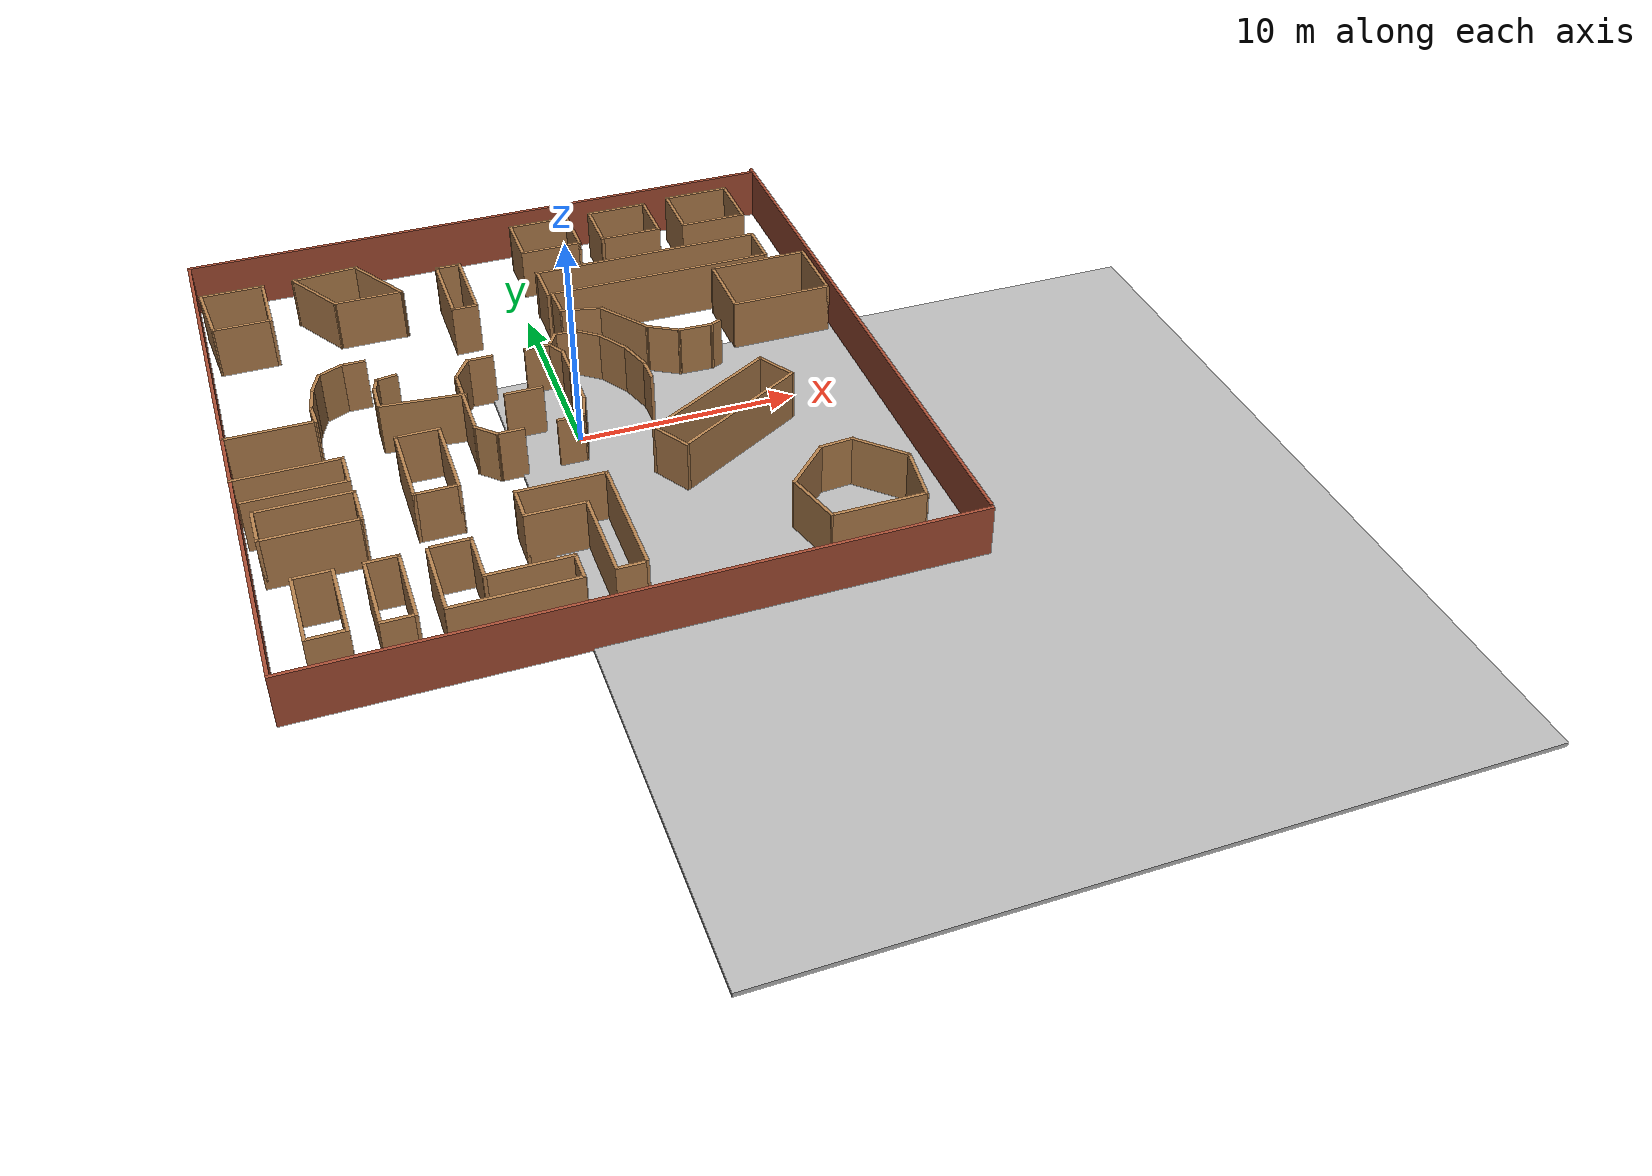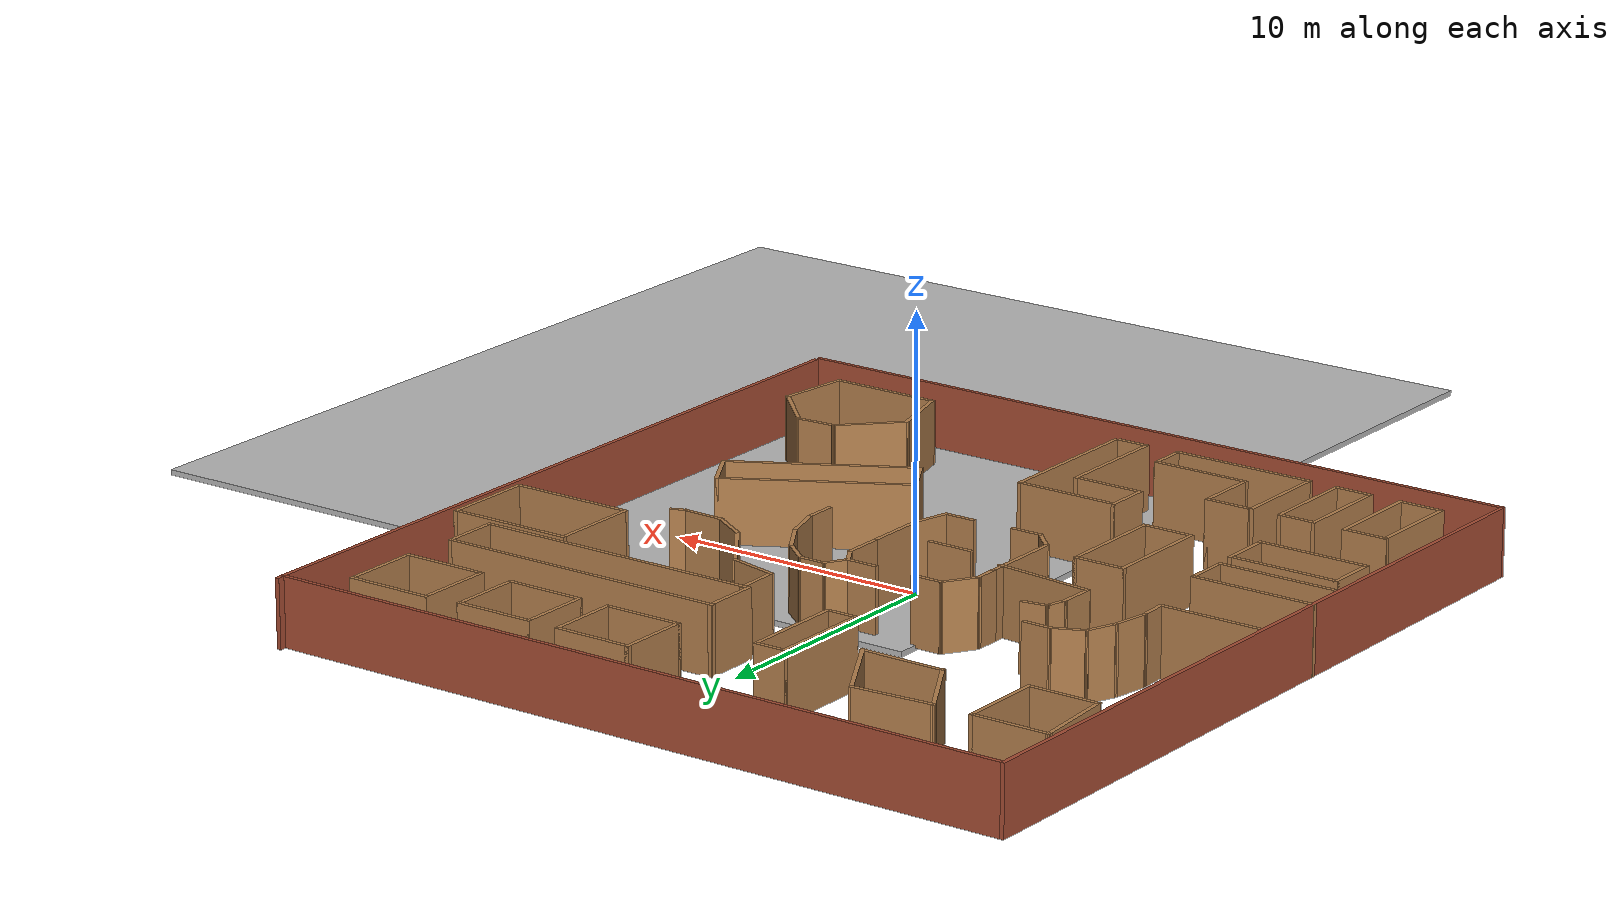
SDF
<sdf version="1.6">
 <world name="default">
  <light name="sun" type="directional">
   <pose>0 0 10 0 -0 0</pose>
   <diffuse>0.8 0.8 0.8 1</diffuse>
   <specular>0.2 0.2 0.2 1</specular>
   <attenuation>
    <range>1000</range>
    <constant>0.9</constant>
    <linear>0.01</linear>
    <quadratic>0.001</quadratic>
   </attenuation>
   <direction>-0.5 0.1 -0.9</direction>
  </light>
  <model name="mud_box">
   <static>1</static>
   <link name="link">
    <collision name="collision"><geometry><box><size>64 70 0.2</size></box></geometry></collision>
    <visual name="visual_1">
     <pose>-2 2.5 0 0 -0 0</pose>
     <cast_shadows>0</cast_shadows>
     <geometry><box><size>32 35 0.2</size></box></geometry>
     <material>
      <script>
       <uri>model://mud_box/materials/scripts</uri>
       <uri>model://mud_box/materials/textures</uri>
       <name>vrc/mud</name>
      </script>
     </material>
    </visual>
   </link>
   <pose>15 -15 0 0 -0 0</pose>
  </model>
  <gravity>0 0 -9.8</gravity>
  <magnetic_field>6e-06 2.3e-05 -4.2e-05</magnetic_field>
  <atmosphere type="adiabatic"/>
  <physics name="default_physics" default="0" type="ode">
   <max_step_size>0.001</max_step_size>
   <real_time_factor>1</real_time_factor>
   <real_time_update_rate>1000</real_time_update_rate>
  </physics>
  <scene><ambient>0.4 0.4 0.4 1</ambient><background>0.7 0.7 0.7 1</background><shadows>1</shadows></scene>
  <spherical_coordinates>
   <surface_model>EARTH_WGS84</surface_model>
   <latitude_deg>0</latitude_deg>
   <longitude_deg>0</longitude_deg>
   <elevation>0</elevation>
   <heading_deg>0</heading_deg>
  </spherical_coordinates>
  <model name="Untitled">
   <pose>-0.599498 1.70429 0 0 -0 0</pose>
   <link name="Wall_101">
    <collision name="Wall_101_Collision">
     <geometry><box><size>3 0.15 2.5</size></box></geometry>
     <pose>0 0 1.25 0 -0 0</pose>
    </collision>
    <visual name="Wall_101_Visual">
     <pose>0 0 1.25 0 -0 0</pose>
     <geometry><box><size>3 0.15 2.5</size></box></geometry>
     <material>
      <script><uri>file://media/materials/scripts/gazebo.material</uri><name>Gazebo/Wood</name></script>
      <ambient>1 1 1 1</ambient>
     </material>
     <meta><layer>0</layer></meta>
    </visual>
    <pose>2.53338 13.315 0 0 -0 3.14159</pose>
   </link>
   <link name="Wall_102">
    <collision name="Wall_102_Collision">
     <geometry><box><size>2.75 0.15 2.5</size></box></geometry>
     <pose>0 0 1.25 0 -0 0</pose>
    </collision>
    <visual name="Wall_102_Visual">
     <pose>0 0 1.25 0 -0 0</pose>
     <geometry><box><size>2.75 0.15 2.5</size></box></geometry>
     <material>
      <script><uri>file://media/materials/scripts/gazebo.material</uri><name>Gazebo/Wood</name></script>
      <ambient>1 1 1 1</ambient>
     </material>
     <meta><layer>0</layer></meta>
    </visual>
    <pose>1.10838 12.015 0 0 0 -1.5708</pose>
   </link>
   <link name="Wall_103">
    <collision name="Wall_103_Collision">
     <geometry><box><size>3 0.15 2.5</size></box></geometry>
     <pose>0 0 1.25 0 -0 0</pose>
    </collision>
    <visual name="Wall_103_Visual">
     <pose>0 0 1.25 0 -0 0</pose>
     <geometry><box><size>3 0.15 2.5</size></box></geometry>
     <material>
      <script><uri>file://media/materials/scripts/gazebo.material</uri><name>Gazebo/Wood</name></script>
      <ambient>1 1 1 1</ambient>
     </material>
     <meta><layer>0</layer></meta>
    </visual>
    <pose>2.53338 10.715 0 0 -0 0</pose>
   </link>
   <link name="Wall_104">
    <collision name="Wall_104_Collision">
     <geometry><box><size>2.75 0.15 2.5</size></box></geometry>
     <pose>0 0 1.25 0 -0 0</pose>
    </collision>
    <visual name="Wall_104_Visual">
     <pose>0 0 1.25 0 -0 0</pose>
     <geometry><box><size>2.75 0.15 2.5</size></box></geometry>
     <material>
      <script><uri>file://media/materials/scripts/gazebo.material</uri><name>Gazebo/Wood</name></script>
      <ambient>1 1 1 1</ambient>
     </material>
     <meta><layer>0</layer></meta>
    </visual>
    <pose>3.95838 12.015 0 0 -0 1.5708</pose>
   </link>
   <link name="Wall_106">
    <collision name="Wall_106_Collision">
     <geometry><box><size>2.17719 0.15 2.5</size></box></geometry>
     <pose>0 0 1.25 0 -0 0</pose>
    </collision>
    <visual name="Wall_106_Visual">
     <pose>0 0 1.25 0 -0 0</pose>
     <geometry><box><size>2.17719 0.15 2.5</size></box></geometry>
     <material>
      <script><uri>file://media/materials/scripts/gazebo.material</uri><name>Gazebo/Wood</name></script>
      <ambient>1 1 1 1</ambient>
     </material>
     <meta><layer>0</layer></meta>
    </visual>
    <pose>1.35118 7.63612 0 0 0 -1.5708</pose>
   </link>
   <link name="Wall_107">
    <collision name="Wall_107_Collision">
     <geometry><box><size>11 0.15 2.5</size></box></geometry>
     <pose>0 0 1.25 0 -0 0</pose>
    </collision>
    <visual name="Wall_107_Visual">
     <pose>0 0 1.25 0 -0 0</pose>
     <geometry><box><size>11 0.15 2.5</size></box></geometry>
     <material>
      <script><uri>file://media/materials/scripts/gazebo.material</uri><name>Gazebo/Wood</name></script>
      <ambient>1 1 1 1</ambient>
     </material>
     <meta><layer>0</layer></meta>
    </visual>
    <pose>6.77618 6.62279 0 0 -0 0</pose>
   </link>
   <link name="Wall_108">
    <collision name="Wall_108_Collision">
     <geometry><box><size>2.17719 0.15 2.5</size></box></geometry>
     <pose>0 0 1.25 0 -0 0</pose>
    </collision>
    <visual name="Wall_108_Visual">
     <pose>0 0 1.25 0 -0 0</pose>
     <geometry><box><size>2.17719 0.15 2.5</size></box></geometry>
     <material>
      <script><uri>file://media/materials/scripts/gazebo.material</uri><name>Gazebo/Wood</name></script>
      <ambient>1 1 1 1</ambient>
     </material>
     <meta><layer>0</layer></meta>
    </visual>
    <pose>12.2012 7.63612 0 0 -0 1.5708</pose>
   </link>
   <link name="Wall_109">
    <collision name="Wall_109_Collision">
     <geometry><box><size>11 0.15 2.5</size></box></geometry>
     <pose>0 0 1.25 0 -0 0</pose>
    </collision>
    <visual name="Wall_109_Visual">
     <pose>0 0 1.25 0 -0 0</pose>
     <geometry><box><size>11 0.15 2.5</size></box></geometry>
     <material>
      <script><uri>file://media/materials/scripts/gazebo.material</uri><name>Gazebo/Wood</name></script>
      <ambient>1 1 1 1</ambient>
     </material>
     <meta><layer>0</layer></meta>
    </visual>
    <pose>6.73044 8.64946 0 0 -0 3.14159</pose>
   </link>
   <link name="Wall_111">
    <collision name="Wall_111_Collision">
     <geometry><box><size>3 0.15 2.5</size></box></geometry>
     <pose>0 0 1.25 0 -0 0</pose>
    </collision>
    <visual name="Wall_111_Visual">
     <pose>0 0 1.25 0 -0 0</pose>
     <geometry><box><size>3 0.15 2.5</size></box></geometry>
     <material>
      <script><uri>file://media/materials/scripts/gazebo.material</uri><name>Gazebo/Wood</name></script>
      <ambient>1 1 1 1</ambient>
     </material>
     <meta><layer>0</layer></meta>
    </visual>
    <pose>-12.6189 11.8842 0 0 -0 0</pose>
   </link>
   <link name="Wall_112">
    <collision name="Wall_112_Collision">
     <geometry><box><size>3.25 0.15 2.5</size></box></geometry>
     <pose>0 0 1.25 0 -0 0</pose>
    </collision>
    <visual name="Wall_112_Visual">
     <pose>0 0 1.25 0 -0 0</pose>
     <geometry><box><size>3.25 0.15 2.5</size></box></geometry>
     <material>
      <script><uri>file://media/materials/scripts/gazebo.material</uri><name>Gazebo/Wood</name></script>
      <ambient>1 1 1 1</ambient>
     </material>
     <meta><layer>0</layer></meta>
    </visual>
    <pose>-11.1939 10.3342 0 0 0 -1.5708</pose>
   </link>
   <link name="Wall_113">
    <collision name="Wall_113_Collision">
     <geometry><box><size>2.75 0.15 2.5</size></box></geometry>
     <pose>0 0 1.25 0 -0 0</pose>
    </collision>
    <visual name="Wall_113_Visual">
     <pose>0 0 1.25 0 -0 0</pose>
     <geometry><box><size>2.75 0.15 2.5</size></box></geometry>
     <material>
      <script><uri>file://media/materials/scripts/gazebo.material</uri><name>Gazebo/Wood</name></script>
      <ambient>1 1 1 1</ambient>
     </material>
     <meta><layer>0</layer></meta>
    </visual>
    <pose>-12.4939 8.78422 0 0 -0 3.14159</pose>
   </link>
   <link name="Wall_114">
    <collision name="Wall_114_Collision">
     <geometry><box><size>3.26006 0.15 2.5</size></box></geometry>
     <pose>0 0 1.25 0 -0 0</pose>
    </collision>
    <visual name="Wall_114_Visual">
     <pose>0 0 1.25 0 -0 0</pose>
     <geometry><box><size>3.26006 0.15 2.5</size></box></geometry>
     <material>
      <script><uri>file://media/materials/scripts/gazebo.material</uri><name>Gazebo/Wood</name></script>
      <ambient>1 1 1 1</ambient>
     </material>
     <meta><layer>0</layer></meta>
    </visual>
    <pose>-13.9189 10.3342 0 0 -0 1.65127</pose>
   </link>
   <link name="Wall_116">
    <collision name="Wall_116_Collision">
     <geometry><box><size>3.25 0.15 2.5</size></box></geometry>
     <pose>0 0 1.25 0 -0 0</pose>
    </collision>
    <visual name="Wall_116_Visual">
     <pose>0 0 1.25 0 -0 0</pose>
     <geometry><box><size>3.25 0.15 2.5</size></box></geometry>
     <material>
      <script><uri>file://media/materials/scripts/gazebo.material</uri><name>Gazebo/Wood</name></script>
      <ambient>1 1 1 1</ambient>
     </material>
     <meta><layer>0</layer></meta>
    </visual>
    <pose>-8.96931 10.5419 0 0 0 -1.0472</pose>
   </link>
   <link name="Wall_117">
    <collision name="Wall_117_Collision">
     <geometry><box><size>3.25 0.15 2.5</size></box></geometry>
     <pose>0 0 1.25 0 -0 0</pose>
    </collision>
    <visual name="Wall_117_Visual">
     <pose>0 0 1.25 0 -0 0</pose>
     <geometry><box><size>3.25 0.15 2.5</size></box></geometry>
     <material>
      <script><uri>file://media/materials/scripts/gazebo.material</uri><name>Gazebo/Wood</name></script>
      <ambient>1 1 1 1</ambient>
     </material>
     <meta><layer>0</layer></meta>
    </visual>
    <pose>-6.64431 9.19954 0 0 -0 0</pose>
   </link>
   <link name="Wall_118">
    <collision name="Wall_118_Collision">
     <geometry><box><size>3.5 0.15 2.5</size></box></geometry>
     <pose>0 0 1.25 0 -0 0</pose>
    </collision>
    <visual name="Wall_118_Visual">
     <pose>0 0 1.25 0 -0 0</pose>
     <geometry><box><size>3.5 0.15 2.5</size></box></geometry>
     <material>
      <script><uri>file://media/materials/scripts/gazebo.material</uri><name>Gazebo/Wood</name></script>
      <ambient>1 1 1 1</ambient>
     </material>
     <meta><layer>0</layer></meta>
    </visual>
    <pose>-5.93181 10.6501 0 0 -0 2.0944</pose>
   </link>
   <link name="Wall_119">
    <collision name="Wall_119_Collision">
     <geometry><box><size>3.13287 0.15 2.5</size></box></geometry>
     <pose>0 0 1.25 0 -0 0</pose>
    </collision>
    <visual name="Wall_119_Visual">
     <pose>0 0 1.25 0 -0 0</pose>
     <geometry><box><size>3.13287 0.15 2.5</size></box></geometry>
     <material>
      <script><uri>file://media/materials/scripts/gazebo.material</uri><name>Gazebo/Wood</name></script>
      <ambient>1 1 1 1</ambient>
     </material>
     <meta><layer>0</layer></meta>
    </visual>
    <pose>-8.25681 11.9925 0 0 0 -3.06894</pose>
   </link>
   <link name="Wall_121">
    <collision name="Wall_121_Collision">
     <geometry><box><size>1.00408 0.15 2.5</size></box></geometry>
     <pose>0 0 1.25 0 -0 0</pose>
    </collision>
    <visual name="Wall_121_Visual">
     <pose>0 0 1.25 0 -0 0</pose>
     <geometry><box><size>1.00408 0.15 2.5</size></box></geometry>
     <material>
      <script><uri>file://media/materials/scripts/gazebo.material</uri><name>Gazebo/Wood</name></script>
      <ambient>1 1 1 1</ambient>
     </material>
     <meta><layer>0</layer></meta>
    </visual>
    <pose>0.604472 2.8259 0 0 -0 1.03717</pose>
   </link>
   <link name="Wall_122">
    <collision name="Wall_122_Collision">
     <geometry><box><size>1.11054 0.15 2.5</size></box></geometry>
     <pose>0 0 1.25 0 -0 0</pose>
    </collision>
    <visual name="Wall_122_Visual">
     <pose>0 0 1.25 0 -0 0</pose>
     <geometry><box><size>1.11054 0.15 2.5</size></box></geometry>
     <material>
      <script><uri>file://media/materials/scripts/gazebo.material</uri><name>Gazebo/Wood</name></script>
      <ambient>1 1 1 1</ambient>
     </material>
     <meta><layer>0</layer></meta>
    </visual>
    <pose>1.30196 3.19357 0 0 -0 0</pose>
   </link>
   <link name="Wall_123">
    <collision name="Wall_123_Collision">
     <geometry><box><size>1.38583 0.15 2.5</size></box></geometry>
     <pose>0 0 1.25 0 -0 0</pose>
    </collision>
    <visual name="Wall_123_Visual">
     <pose>0 0 1.25 0 -0 0</pose>
     <geometry><box><size>1.38583 0.15 2.5</size></box></geometry>
     <material>
      <script><uri>file://media/materials/scripts/gazebo.material</uri><name>Gazebo/Wood</name></script>
      <ambient>1 1 1 1</ambient>
     </material>
     <meta><layer>0</layer></meta>
    </visual>
    <pose>2.26251 2.80478 0 0 0 -0.680521</pose>
   </link>
   <link name="Wall_124">
    <collision name="Wall_124_Collision">
     <geometry><box><size>1.71121 0.15 2.5</size></box></geometry>
     <pose>0 0 1.25 0 -0 0</pose>
    </collision>
    <visual name="Wall_124_Visual">
     <pose>0 0 1.25 0 -0 0</pose>
     <geometry><box><size>1.71121 0.15 2.5</size></box></geometry>
     <material>
      <script><uri>file://media/materials/scripts/gazebo.material</uri><name>Gazebo/Wood</name></script>
      <ambient>1 1 1 1</ambient>
     </material>
     <meta><layer>0</layer></meta>
    </visual>
    <pose>3.15444 1.75275 0 0 0 -1.0153</pose>
   </link>
   <link name="Wall_125">
    <collision name="Wall_125_Collision">
     <geometry><box><size>1.68349 0.15 2.5</size></box></geometry>
     <pose>0 0 1.25 0 -0 0</pose>
    </collision>
    <visual name="Wall_125_Visual">
     <pose>0 0 1.25 0 -0 0</pose>
     <geometry><box><size>1.68349 0.15 2.5</size></box></geometry>
     <material>
      <script><uri>file://media/materials/scripts/gazebo.material</uri><name>Gazebo/Wood</name></script>
      <ambient>1 1 1 1</ambient>
     </material>
     <meta><layer>0</layer></meta>
    </visual>
    <pose>3.79481 0.357676 0 0 0 -1.26791</pose>
   </link>
   <link name="Wall_126">
    <collision name="Wall_126_Collision">
     <geometry><box><size>1.24777 0.15 2.5</size></box></geometry>
     <pose>0 0 1.25 0 -0 0</pose>
    </collision>
    <visual name="Wall_126_Visual">
     <pose>0 0 1.25 0 -0 0</pose>
     <geometry><box><size>1.24777 0.15 2.5</size></box></geometry>
     <material>
      <script><uri>file://media/materials/scripts/gazebo.material</uri><name>Gazebo/Wood</name></script>
      <ambient>1 1 1 1</ambient>
     </material>
     <meta><layer>0</layer></meta>
    </visual>
    <pose>4.02351 -0.923051 0 0 0 -1.5708</pose>
   </link>
   <link name="Wall_128">
    <collision name="Wall_128_Collision">
     <geometry><box><size>1.75156 0.15 2.5</size></box></geometry>
     <pose>0 0 1.25 0 -0 0</pose>
    </collision>
    <visual name="Wall_128_Visual">
     <pose>0 0 1.25 0 -0 0</pose>
     <geometry><box><size>1.75156 0.15 2.5</size></box></geometry>
     <material>
      <script><uri>file://media/materials/scripts/gazebo.material</uri><name>Gazebo/Wood</name></script>
      <ambient>1 1 1 1</ambient>
     </material>
     <meta><layer>0</layer></meta>
    </visual>
    <pose>1.5764 5.86938 0 0 0 -1.54223</pose>
   </link>
   <link name="Wall_129">
    <collision name="Wall_129_Collision">
     <geometry><box><size>1.98075 0.15 2.5</size></box></geometry>
     <pose>0 0 1.25 0 -0 0</pose>
    </collision>
    <visual name="Wall_129_Visual">
     <pose>0 0 1.25 0 -0 0</pose>
     <geometry><box><size>1.98075 0.15 2.5</size></box></geometry>
     <material>
      <script><uri>file://media/materials/scripts/gazebo.material</uri><name>Gazebo/Wood</name></script>
      <ambient>1 1 1 1</ambient>
     </material>
     <meta><layer>0</layer></meta>
    </visual>
    <pose>2.49121 4.86309 0 0 0 -0.226799</pose>
   </link>
   <link name="Wall_13">
    <collision name="Wall_13_Collision">
     <geometry><box><size>1 0.15 2.5</size></box></geometry>
     <pose>0 0 1.25 0 -0 0</pose>
    </collision>
    <visual name="Wall_13_Visual">
     <pose>0 0 1.25 0 -0 0</pose>
     <geometry><box><size>1 0.15 2.5</size></box></geometry>
     <material>
      <script><uri>file://media/materials/scripts/gazebo.material</uri><name>Gazebo/Wood</name></script>
      <ambient>1 1 1 1</ambient>
     </material>
     <meta><layer>0</layer></meta>
    </visual>
    <pose>-4.09355 0.934302 0 0 -0 1.5708</pose>
   </link>
   <link name="Wall_130">
    <collision name="Wall_130_Collision">
     <geometry><box><size>2.90431 0.15 2.5</size></box></geometry>
     <pose>0 0 1.25 0 -0 0</pose>
    </collision>
    <visual name="Wall_130_Visual">
     <pose>0 0 1.25 0 -0 0</pose>
     <geometry><box><size>2.90431 0.15 2.5</size></box></geometry>
     <material>
      <script><uri>file://media/materials/scripts/gazebo.material</uri><name>Gazebo/Wood</name></script>
      <ambient>1 1 1 1</ambient>
     </material>
     <meta><layer>0</layer></meta>
    </visual>
    <pose>4.1836 3.53662 0 0 0 -0.950547</pose>
   </link>
   <link name="Wall_131">
    <collision name="Wall_131_Collision">
     <geometry><box><size>1.6483 0.15 2.5</size></box></geometry>
     <pose>0 0 1.25 0 -0 0</pose>
    </collision>
    <visual name="Wall_131_Visual">
     <pose>0 0 1.25 0 -0 0</pose>
     <geometry><box><size>1.6483 0.15 2.5</size></box></geometry>
     <material>
      <script><uri>file://media/materials/scripts/gazebo.material</uri><name>Gazebo/Wood</name></script>
      <ambient>1 1 1 1</ambient>
     </material>
     <meta><layer>0</layer></meta>
    </visual>
    <pose>5.62442 2.0272 0 0 0 -0.545655</pose>
   </link>
   <link name="Wall_132">
    <collision name="Wall_132_Collision">
     <geometry><box><size>1.66012 0.15 2.5</size></box></geometry>
     <pose>0 0 1.25 0 -0 0</pose>
    </collision>
    <visual name="Wall_132_Visual">
     <pose>0 0 1.25 0 -0 0</pose>
     <geometry><box><size>1.66012 0.15 2.5</size></box></geometry>
     <material>
      <script><uri>file://media/materials/scripts/gazebo.material</uri><name>Gazebo/Wood</name></script>
      <ambient>1 1 1 1</ambient>
     </material>
     <meta><layer>0</layer></meta>
    </visual>
    <pose>7.0195 1.61553 0 0 0 -0.030294</pose>
   </link>
   <link name="Wall_133">
    <collision name="Wall_133_Collision">
     <geometry><box><size>0.642638 0.15 2.5</size></box></geometry>
     <pose>0 0 1.25 0 -0 0</pose>
    </collision>
    <visual name="Wall_133_Visual">
     <pose>0 0 1.25 0 -0 0</pose>
     <geometry><box><size>0.642638 0.15 2.5</size></box></geometry>
     <material>
      <script><uri>file://media/materials/scripts/gazebo.material</uri><name>Gazebo/Wood</name></script>
      <ambient>1 1 1 1</ambient>
     </material>
     <meta><layer>0</layer></meta>
    </visual>
    <pose>8.00291 1.68414 0 0 -0 0.380506</pose>
   </link>
   <link name="Wall_135">
    <collision name="Wall_135_Collision">
     <geometry><box><size>3.5 0.15 2.5</size></box></geometry>
     <pose>0 0 1.25 0 -0 0</pose>
    </collision>
    <visual name="Wall_135_Visual">
     <pose>0 0 1.25 0 -0 0</pose>
     <geometry><box><size>3.5 0.15 2.5</size></box></geometry>
     <material>
      <script><uri>file://media/materials/scripts/gazebo.material</uri><name>Gazebo/Wood</name></script>
      <ambient>1 1 1 1</ambient>
     </material>
     <meta><layer>0</layer></meta>
    </visual>
    <pose>9.37512 4.53743 0 0 0 -1.5708</pose>
   </link>
   <link name="Wall_136">
    <collision name="Wall_136_Collision">
     <geometry><box><size>4.75 0.15 2.5</size></box></geometry>
     <pose>0 0 1.25 0 -0 0</pose>
    </collision>
    <visual name="Wall_136_Visual">
     <pose>0 0 1.25 0 -0 0</pose>
     <geometry><box><size>4.75 0.15 2.5</size></box></geometry>
     <material>
      <script><uri>file://media/materials/scripts/gazebo.material</uri><name>Gazebo/Wood</name></script>
      <ambient>1 1 1 1</ambient>
     </material>
     <meta><layer>0</layer></meta>
    </visual>
    <pose>11.6751 2.86243 0 0 -0 0</pose>
   </link>
   <link name="Wall_137">
    <collision name="Wall_137_Collision">
     <geometry><box><size>3.5 0.15 2.5</size></box></geometry>
     <pose>0 0 1.25 0 -0 0</pose>
    </collision>
    <visual name="Wall_137_Visual">
     <pose>0 0 1.25 0 -0 0</pose>
     <geometry><box><size>3.5 0.15 2.5</size></box></geometry>
     <material>
      <script><uri>file://media/materials/scripts/gazebo.material</uri><name>Gazebo/Wood</name></script>
      <ambient>1 1 1 1</ambient>
     </material>
     <meta><layer>0</layer></meta>
    </visual>
    <pose>13.9751 4.53743 0 0 -0 1.5708</pose>
   </link>
   <link name="Wall_138">
    <collision name="Wall_138_Collision">
     <geometry><box><size>4.75 0.15 2.5</size></box></geometry>
     <pose>0 0 1.25 0 -0 0</pose>
    </collision>
    <visual name="Wall_138_Visual">
     <pose>0 0 1.25 0 -0 0</pose>
     <geometry><box><size>4.75 0.15 2.5</size></box></geometry>
     <material>
      <script><uri>file://media/materials/scripts/gazebo.material</uri><name>Gazebo/Wood</name></script>
      <ambient>1 1 1 1</ambient>
     </material>
     <meta><layer>0</layer></meta>
    </visual>
    <pose>11.6751 6.21243 0 0 -0 3.14159</pose>
   </link>
   <link name="Wall_14">
    <collision name="Wall_14_Collision">
     <geometry><box><size>1.46157 0.15 2.5</size></box></geometry>
     <pose>0 0 1.25 0 -0 0</pose>
    </collision>
    <visual name="Wall_14_Visual">
     <pose>0 0 1.25 0 -0 0</pose>
     <geometry><box><size>1.46157 0.15 2.5</size></box></geometry>
     <material>
      <script><uri>file://media/materials/scripts/gazebo.material</uri><name>Gazebo/Wood</name></script>
      <ambient>1 1 1 1</ambient>
     </material>
     <meta><layer>0</layer></meta>
    </visual>
    <pose>-3.73558 1.90877 0 0 -0 0.99338</pose>
   </link>
   <link name="Wall_140">
    <collision name="Wall_140_Collision">
     <geometry><box><size>7 0.15 2.5</size></box></geometry>
     <pose>0 0 1.25 0 -0 0</pose>
    </collision>
    <visual name="Wall_140_Visual">
     <pose>0 0 1.25 0 -0 0</pose>
     <geometry><box><size>7 0.15 2.5</size></box></geometry>
     <material>
      <script><uri>file://media/materials/scripts/gazebo.material</uri><name>Gazebo/Wood</name></script>
      <ambient>1 1 1 1</ambient>
     </material>
     <meta><layer>0</layer></meta>
    </visual>
    <pose>6.04306 -3.45888 0 0 0 -2.61799</pose>
   </link>
   <link name="Wall_141">
    <collision name="Wall_141_Collision">
     <geometry><box><size>2 0.15 2.5</size></box></geometry>
     <pose>0 0 1.25 0 -0 0</pose>
    </collision>
    <visual name="Wall_141_Visual">
     <pose>0 0 1.25 0 -0 0</pose>
     <geometry><box><size>2 0.15 2.5</size></box></geometry>
     <material>
      <script><uri>file://media/materials/scripts/gazebo.material</uri><name>Gazebo/Wood</name></script>
      <ambient>1 1 1 1</ambient>
     </material>
     <meta><layer>0</layer></meta>
    </visual>
    <pose>3.53942 -5.97245 0 0 0 -1.0472</pose>
   </link>
   <link name="Wall_142">
    <collision name="Wall_142_Collision">
     <geometry><box><size>7 0.15 2.5</size></box></geometry>
     <pose>0 0 1.25 0 -0 0</pose>
    </collision>
    <visual name="Wall_142_Visual">
     <pose>0 0 1.25 0 -0 0</pose>
     <geometry><box><size>7 0.15 2.5</size></box></geometry>
     <material>
      <script><uri>file://media/materials/scripts/gazebo.material</uri><name>Gazebo/Wood</name></script>
      <ambient>1 1 1 1</ambient>
     </material>
     <meta><layer>0</layer></meta>
    </visual>
    <pose>6.96806 -5.06102 0 0 -0 0.523599</pose>
   </link>
   <link name="Wall_143">
    <collision name="Wall_143_Collision">
     <geometry><box><size>2 0.15 2.5</size></box></geometry>
     <pose>0 0 1.25 0 -0 0</pose>
    </collision>
    <visual name="Wall_143_Visual">
     <pose>0 0 1.25 0 -0 0</pose>
     <geometry><box><size>2 0.15 2.5</size></box></geometry>
     <material>
      <script><uri>file://media/materials/scripts/gazebo.material</uri><name>Gazebo/Wood</name></script>
      <ambient>1 1 1 1</ambient>
     </material>
     <meta><layer>0</layer></meta>
    </visual>
    <pose>9.4717 -2.54745 0 0 -0 2.0944</pose>
   </link>
   <link name="Wall_145">
    <collision name="Wall_145_Collision">
     <geometry><box><size>4 0.15 2.5</size></box></geometry>
     <pose>0 0 1.25 0 -0 0</pose>
    </collision>
    <visual name="Wall_145_Visual">
     <pose>0 0 1.25 0 -0 0</pose>
     <geometry><box><size>4 0.15 2.5</size></box></geometry>
     <material>
      <script><uri>file://media/materials/scripts/gazebo.material</uri><name>Gazebo/Wood</name></script>
      <ambient>1 1 1 1</ambient>
     </material>
     <meta><layer>0</layer></meta>
    </visual>
    <pose>-3.11197 8.76998 0 0 0 -1.5708</pose>
   </link>
   <link name="Wall_146">
    <collision name="Wall_146_Collision">
     <geometry><box><size>1.25 0.15 2.5</size></box></geometry>
     <pose>0 0 1.25 0 -0 0</pose>
    </collision>
    <visual name="Wall_146_Visual">
     <pose>0 0 1.25 0 -0 0</pose>
     <geometry><box><size>1.25 0.15 2.5</size></box></geometry>
     <material>
      <script><uri>file://media/materials/scripts/gazebo.material</uri><name>Gazebo/Wood</name></script>
      <ambient>1 1 1 1</ambient>
     </material>
     <meta><layer>0</layer></meta>
    </visual>
    <pose>-2.56197 6.84497 0 0 -0 0</pose>
   </link>
   <link name="Wall_147">
    <collision name="Wall_147_Collision">
     <geometry><box><size>4 0.15 2.5</size></box></geometry>
     <pose>0 0 1.25 0 -0 0</pose>
    </collision>
    <visual name="Wall_147_Visual">
     <pose>0 0 1.25 0 -0 0</pose>
     <geometry><box><size>4 0.15 2.5</size></box></geometry>
     <material>
      <script><uri>file://media/materials/scripts/gazebo.material</uri><name>Gazebo/Wood</name></script>
      <ambient>1 1 1 1</ambient>
     </material>
     <meta><layer>0</layer></meta>
    </visual>
    <pose>-2.01197 8.76998 0 0 -0 1.5708</pose>
   </link>
   <link name="Wall_148">
    <collision name="Wall_148_Collision">
     <geometry><box><size>1.25 0.15 2.5</size></box></geometry>
     <pose>0 0 1.25 0 -0 0</pose>
    </collision>
    <visual name="Wall_148_Visual">
     <pose>0 0 1.25 0 -0 0</pose>
     <geometry><box><size>1.25 0.15 2.5</size></box></geometry>
     <material>
      <script><uri>file://media/materials/scripts/gazebo.material</uri><name>Gazebo/Wood</name></script>
      <ambient>1 1 1 1</ambient>
     </material>
     <meta><layer>0</layer></meta>
    </visual>
    <pose>-2.56197 10.695 0 0 -0 3.14159</pose>
   </link>
   <link name="Wall_15">
    <collision name="Wall_15_Collision">
     <geometry><box><size>1.25 0.15 2.5</size></box></geometry>
     <pose>0 0 1.25 0 -0 0</pose>
    </collision>
    <visual name="Wall_15_Visual">
     <pose>0 0 1.25 0 -0 0</pose>
     <geometry><box><size>1.25 0.15 2.5</size></box></geometry>
     <material>
      <script><uri>file://media/materials/scripts/gazebo.material</uri><name>Gazebo/Wood</name></script>
      <ambient>1 1 1 1</ambient>
     </material>
     <meta><layer>0</layer></meta>
    </visual>
    <pose>-2.82761 2.45824 0 0 -0 0</pose>
   </link>
   <link name="Wall_17">
    <collision name="Wall_17_Collision">
     <geometry><box><size>1.25 0.15 2.5</size></box></geometry>
     <pose>0 0 1.25 0 -0 0</pose>
    </collision>
    <visual name="Wall_17_Visual">
     <pose>0 0 1.25 0 -0 0</pose>
     <geometry><box><size>1.25 0.15 2.5</size></box></geometry>
     <material>
      <script><uri>file://media/materials/scripts/gazebo.material</uri><name>Gazebo/Wood</name></script>
      <ambient>1 1 1 1</ambient>
     </material>
     <meta><layer>0</layer></meta>
    </visual>
    <pose>-0.162746 2.45824 0 0 -0 0</pose>
   </link>
   <link name="Wall_18">
    <collision name="Wall_18_Collision">
     <geometry><box><size>1 0.15 2.5</size></box></geometry>
     <pose>0 0 1.25 0 -0 0</pose>
    </collision>
    <visual name="Wall_18_Visual">
     <pose>0 0 1.25 0 -0 0</pose>
     <geometry><box><size>1 0.15 2.5</size></box></geometry>
     <material>
      <script><uri>file://media/materials/scripts/gazebo.material</uri><name>Gazebo/Wood</name></script>
      <ambient>1 1 1 1</ambient>
     </material>
     <meta><layer>0</layer></meta>
    </visual>
    <pose>0.599754 2.09017 0 0 0 -1.0472</pose>
   </link>
   <link name="Wall_19">
    <collision name="Wall_19_Collision">
     <geometry><box><size>1.5 0.15 2.5</size></box></geometry>
     <pose>0 0 1.25 0 -0 0</pose>
    </collision>
    <visual name="Wall_19_Visual">
     <pose>0 0 1.25 0 -0 0</pose>
     <geometry><box><size>1.5 0.15 2.5</size></box></geometry>
     <material>
      <script><uri>file://media/materials/scripts/gazebo.material</uri><name>Gazebo/Wood</name></script>
      <ambient>1 1 1 1</ambient>
     </material>
     <meta><layer>0</layer></meta>
    </visual>
    <pose>0.812254 1.04711 0 0 0 -1.5708</pose>
   </link>
   <link name="Wall_20">
    <collision name="Wall_20_Collision">
     <geometry><box><size>2.5 0.15 2.5</size></box></geometry>
     <pose>0 0 1.25 0 -0 0</pose>
    </collision>
    <visual name="Wall_20_Visual">
     <pose>0 0 1.25 0 -0 0</pose>
     <geometry><box><size>2.5 0.15 2.5</size></box></geometry>
     <material>
      <script><uri>file://media/materials/scripts/gazebo.material</uri><name>Gazebo/Wood</name></script>
      <ambient>1 1 1 1</ambient>
     </material>
     <meta><layer>0</layer></meta>
    </visual>
    <pose>0.812254 -0.802886 0 0 0 -1.5708</pose>
   </link>
   <link name="Wall_21">
    <collision name="Wall_21_Collision">
     <geometry><box><size>1.5 0.15 2.5</size></box></geometry>
     <pose>0 0 1.25 0 -0 0</pose>
    </collision>
    <visual name="Wall_21_Visual">
     <pose>0 0 1.25 0 -0 0</pose>
     <geometry><box><size>1.5 0.15 2.5</size></box></geometry>
     <material>
      <script><uri>file://media/materials/scripts/gazebo.material</uri><name>Gazebo/Wood</name></script>
      <ambient>1 1 1 1</ambient>
     </material>
     <meta><layer>0</layer></meta>
    </visual>
    <pose>0.637551 -2.62989 0 0 0 -1.8326</pose>
   </link>
   <link name="Wall_22">
    <collision name="Wall_22_Collision">
     <geometry><box><size>1.25 0.15 2.5</size></box></geometry>
     <pose>0 0 1.25 0 -0 0</pose>
    </collision>
    <visual name="Wall_22_Visual">
     <pose>0 0 1.25 0 -0 0</pose>
     <geometry><box><size>1.25 0.15 2.5</size></box></geometry>
     <material>
      <script><uri>file://media/materials/scripts/gazebo.material</uri><name>Gazebo/Wood</name></script>
      <ambient>1 1 1 1</ambient>
     </material>
     <meta><layer>0</layer></meta>
    </visual>
    <pose>-0.087152 -3.28189 0 0 -0 3.14159</pose>
   </link>
   <link name="Wall_24">
    <collision name="Wall_24_Collision">
     <geometry><box><size>3.25 0.15 2.5</size></box></geometry>
     <pose>0 0 1.25 0 -0 0</pose>
    </collision>
    <visual name="Wall_24_Visual">
     <pose>0 0 1.25 0 -0 0</pose>
     <geometry><box><size>3.25 0.15 2.5</size></box></geometry>
     <material>
      <script><uri>file://media/materials/scripts/gazebo.material</uri><name>Gazebo/Wood</name></script>
      <ambient>1 1 1 1</ambient>
     </material>
     <meta><layer>0</layer></meta>
    </visual>
    <pose>-4.09355 -1.0407 0 0 0 -1.5708</pose>
   </link>
   <link name="Wall_25">
    <collision name="Wall_25_Collision">
     <geometry><box><size>1.25 0.15 2.5</size></box></geometry>
     <pose>0 0 1.25 0 -0 0</pose>
    </collision>
    <visual name="Wall_25_Visual">
     <pose>0 0 1.25 0 -0 0</pose>
     <geometry><box><size>1.25 0.15 2.5</size></box></geometry>
     <material>
      <script><uri>file://media/materials/scripts/gazebo.material</uri><name>Gazebo/Wood</name></script>
      <ambient>1 1 1 1</ambient>
     </material>
     <meta><layer>0</layer></meta>
    </visual>
    <pose>-3.70464 -2.97961 0 0 0 -0.785398</pose>
   </link>
   <link name="Wall_26">
    <collision name="Wall_26_Collision">
     <geometry><box><size>1.25 0.15 2.5</size></box></geometry>
     <pose>0 0 1.25 0 -0 0</pose>
    </collision>
    <visual name="Wall_26_Visual">
     <pose>0 0 1.25 0 -0 0</pose>
     <geometry><box><size>1.25 0.15 2.5</size></box></geometry>
     <material>
      <script><uri>file://media/materials/scripts/gazebo.material</uri><name>Gazebo/Wood</name></script>
      <ambient>1 1 1 1</ambient>
     </material>
     <meta><layer>0</layer></meta>
    </visual>
    <pose>-2.76573 -3.36851 0 0 -0 0</pose>
   </link>
   <link name="Wall_28">
    <collision name="Wall_28_Collision">
     <geometry><box><size>1.75 0.15 2.5</size></box></geometry>
     <pose>0 0 1.25 0 -0 0</pose>
    </collision>
    <visual name="Wall_28_Visual">
     <pose>0 0 1.25 0 -0 0</pose>
     <geometry><box><size>1.75 0.15 2.5</size></box></geometry>
     <material>
      <script><uri>file://media/materials/scripts/gazebo.material</uri><name>Gazebo/Wood</name></script>
      <ambient>1 1 1 1</ambient>
     </material>
     <meta><layer>0</layer></meta>
    </visual>
    <pose>-1.54349 -0.644148 0 0 -0 0</pose>
   </link>
   <link name="Wall_30">
    <collision name="Wall_30_Collision">
     <geometry><box><size>3.75 0.15 2.5</size></box></geometry>
     <pose>0 0 1.25 0 -0 0</pose>
    </collision>
    <visual name="Wall_30_Visual">
     <pose>0 0 1.25 0 -0 0</pose>
     <geometry><box><size>3.75 0.15 2.5</size></box></geometry>
     <material>
      <script><uri>file://media/materials/scripts/gazebo.material</uri><name>Gazebo/Wood</name></script>
      <ambient>1 1 1 1</ambient>
     </material>
     <meta><layer>0</layer></meta>
    </visual>
    <pose>-12.8041 -11.632 0 0 0 -1.5708</pose>
   </link>
   <link name="Wall_31">
    <collision name="Wall_31_Collision">
     <geometry><box><size>1.75 0.15 2.5</size></box></geometry>
     <pose>0 0 1.25 0 -0 0</pose>
    </collision>
    <visual name="Wall_31_Visual">
     <pose>0 0 1.25 0 -0 0</pose>
     <geometry><box><size>1.75 0.15 2.5</size></box></geometry>
     <material>
      <script><uri>file://media/materials/scripts/gazebo.material</uri><name>Gazebo/Wood</name></script>
      <ambient>1 1 1 1</ambient>
     </material>
     <meta><layer>0</layer></meta>
    </visual>
    <pose>-12.0041 -13.432 0 0 -0 0</pose>
   </link>
   <link name="Wall_32">
    <collision name="Wall_32_Collision">
     <geometry><box><size>3.75 0.15 2.5</size></box></geometry>
     <pose>0 0 1.25 0 -0 0</pose>
    </collision>
    <visual name="Wall_32_Visual">
     <pose>0 0 1.25 0 -0 0</pose>
     <geometry><box><size>3.75 0.15 2.5</size></box></geometry>
     <material>
      <script><uri>file://media/materials/scripts/gazebo.material</uri><name>Gazebo/Wood</name></script>
      <ambient>1 1 1 1</ambient>
     </material>
     <meta><layer>0</layer></meta>
    </visual>
    <pose>-11.2041 -11.632 0 0 -0 1.5708</pose>
   </link>
   <link name="Wall_33">
    <collision name="Wall_33_Collision">
     <geometry><box><size>1.75 0.15 2.5</size></box></geometry>
     <pose>0 0 1.25 0 -0 0</pose>
    </collision>
    <visual name="Wall_33_Visual">
     <pose>0 0 1.25 0 -0 0</pose>
     <geometry><box><size>1.75 0.15 2.5</size></box></geometry>
     <material>
      <script><uri>file://media/materials/scripts/gazebo.material</uri><name>Gazebo/Wood</name></script>
      <ambient>1 1 1 1</ambient>
     </material>
     <meta><layer>0</layer></meta>
    </visual>
    <pose>-12.0041 -9.83197 0 0 -0 3.14159</pose>
   </link>
   <link name="Wall_35">
    <collision name="Wall_35_Collision">
     <geometry><box><size>3.75 0.15 2.5</size></box></geometry>
     <pose>0 0 1.25 0 -0 0</pose>
    </collision>
    <visual name="Wall_35_Visual">
     <pose>0 0 1.25 0 -0 0</pose>
     <geometry><box><size>3.75 0.15 2.5</size></box></geometry>
     <material>
      <script><uri>file://media/materials/scripts/gazebo.material</uri><name>Gazebo/Wood</name></script>
      <ambient>1 1 1 1</ambient>
     </material>
     <meta><layer>0</layer></meta>
    </visual>
    <pose>-10.0046 -11.6426 0 0 0 -1.5708</pose>
   </link>
   <link name="Wall_36">
    <collision name="Wall_36_Collision">
     <geometry><box><size>1.5 0.15 2.5</size></box></geometry>
     <pose>0 0 1.25 0 -0 0</pose>
    </collision>
    <visual name="Wall_36_Visual">
     <pose>0 0 1.25 0 -0 0</pose>
     <geometry><box><size>1.5 0.15 2.5</size></box></geometry>
     <material>
      <script><uri>file://media/materials/scripts/gazebo.material</uri><name>Gazebo/Wood</name></script>
      <ambient>1 1 1 1</ambient>
     </material>
     <meta><layer>0</layer></meta>
    </visual>
    <pose>-9.32959 -13.4426 0 0 -0 0</pose>
   </link>
   <link name="Wall_37">
    <collision name="Wall_37_Collision">
     <geometry><box><size>3.75 0.15 2.5</size></box></geometry>
     <pose>0 0 1.25 0 -0 0</pose>
    </collision>
    <visual name="Wall_37_Visual">
     <pose>0 0 1.25 0 -0 0</pose>
     <geometry><box><size>3.75 0.15 2.5</size></box></geometry>
     <material>
      <script><uri>file://media/materials/scripts/gazebo.material</uri><name>Gazebo/Wood</name></script>
      <ambient>1 1 1 1</ambient>
     </material>
     <meta><layer>0</layer></meta>
    </visual>
    <pose>-8.65459 -11.6426 0 0 -0 1.5708</pose>
   </link>
   <link name="Wall_38">
    <collision name="Wall_38_Collision">
     <geometry><box><size>1.5 0.15 2.5</size></box></geometry>
     <pose>0 0 1.25 0 -0 0</pose>
    </collision>
    <visual name="Wall_38_Visual">
     <pose>0 0 1.25 0 -0 0</pose>
     <geometry><box><size>1.5 0.15 2.5</size></box></geometry>
     <material>
      <script><uri>file://media/materials/scripts/gazebo.material</uri><name>Gazebo/Wood</name></script>
      <ambient>1 1 1 1</ambient>
     </material>
     <meta><layer>0</layer></meta>
    </visual>
    <pose>-9.32959 -9.84261 0 0 -0 3.14159</pose>
   </link>
   <link name="Wall_4">
    <collision name="Wall_4_Collision">
     <geometry><box><size>29.75 0.15 2.5</size></box></geometry>
     <pose>0 0 1.25 0 -0 0</pose>
    </collision>
    <visual name="Wall_4_Visual">
     <pose>0 0 1.25 0 -0 0</pose>
     <geometry><box><size>29.75 0.15 2.5</size></box></geometry>
     <material>
      <script><uri>file://media/materials/scripts/gazebo.material</uri><name>Gazebo/Bricks</name></script>
      <ambient>1 1 1 1</ambient>
     </material>
     <meta><layer>0</layer></meta>
    </visual>
    <pose>14.3279 0.124759 0 0 0 -1.5708</pose>
   </link>
   <link name="Wall_40">
    <collision name="Wall_40_Collision">
     <geometry><box><size>3.75 0.15 2.5</size></box></geometry>
     <pose>0 0 1.25 0 -0 0</pose>
    </collision>
    <visual name="Wall_40_Visual">
     <pose>0 0 1.25 0 -0 0</pose>
     <geometry><box><size>3.75 0.15 2.5</size></box></geometry>
     <material>
      <script><uri>file://media/materials/scripts/gazebo.material</uri><name>Gazebo/Wood</name></script>
      <ambient>1 1 1 1</ambient>
     </material>
     <meta><layer>0</layer></meta>
    </visual>
    <pose>-7.54896 -11.6772 0 0 0 -1.5708</pose>
   </link>
   <link name="Wall_41">
    <collision name="Wall_41_Collision">
     <geometry><box><size>5.5 0.15 2.5</size></box></geometry>
     <pose>0 0 1.25 0 -0 0</pose>
    </collision>
    <visual name="Wall_41_Visual">
     <pose>0 0 1.25 0 -0 0</pose>
     <geometry><box><size>5.5 0.15 2.5</size></box></geometry>
     <material>
      <script><uri>file://media/materials/scripts/gazebo.material</uri><name>Gazebo/Wood</name></script>
      <ambient>1 1 1 1</ambient>
     </material>
     <meta><layer>0</layer></meta>
    </visual>
    <pose>-4.87397 -13.4772 0 0 -0 0</pose>
   </link>
   <link name="Wall_42">
    <collision name="Wall_42_Collision">
     <geometry><box><size>1.5 0.15 2.5</size></box></geometry>
     <pose>0 0 1.25 0 -0 0</pose>
    </collision>
    <visual name="Wall_42_Visual">
     <pose>0 0 1.25 0 -0 0</pose>
     <geometry><box><size>1.5 0.15 2.5</size></box></geometry>
     <material>
      <script><uri>file://media/materials/scripts/gazebo.material</uri><name>Gazebo/Wood</name></script>
      <ambient>1 1 1 1</ambient>
     </material>
     <meta><layer>0</layer></meta>
    </visual>
    <pose>-2.19897 -12.8022 0 0 -0 1.5708</pose>
   </link>
   <link name="Wall_43">
    <collision name="Wall_43_Collision">
     <geometry><box><size>3.75 0.15 2.5</size></box></geometry>
     <pose>0 0 1.25 0 -0 0</pose>
    </collision>
    <visual name="Wall_43_Visual">
     <pose>0 0 1.25 0 -0 0</pose>
     <geometry><box><size>3.75 0.15 2.5</size></box></geometry>
     <material>
      <script><uri>file://media/materials/scripts/gazebo.material</uri><name>Gazebo/Wood</name></script>
      <ambient>1 1 1 1</ambient>
     </material>
     <meta><layer>0</layer></meta>
    </visual>
    <pose>-3.99897 -12.1272 0 0 -0 3.14159</pose>
   </link>
   <link name="Wall_44">
    <collision name="Wall_44_Collision">
     <geometry><box><size>2.5 0.15 2.5</size></box></geometry>
     <pose>0 0 1.25 0 -0 0</pose>
    </collision>
    <visual name="Wall_44_Visual">
     <pose>0 0 1.25 0 -0 0</pose>
     <geometry><box><size>2.5 0.15 2.5</size></box></geometry>
     <material>
      <script><uri>file://media/materials/scripts/gazebo.material</uri><name>Gazebo/Wood</name></script>
      <ambient>1 1 1 1</ambient>
     </material>
     <meta><layer>0</layer></meta>
    </visual>
    <pose>-5.79897 -10.9522 0 0 -0 1.5708</pose>
   </link>
   <link name="Wall_45">
    <collision name="Wall_45_Collision">
     <geometry><box><size>1.75 0.15 2.5</size></box></geometry>
     <pose>0 0 1.25 0 -0 0</pose>
    </collision>
    <visual name="Wall_45_Visual">
     <pose>0 0 1.25 0 -0 0</pose>
     <geometry><box><size>1.75 0.15 2.5</size></box></geometry>
     <material>
      <script><uri>file://media/materials/scripts/gazebo.material</uri><name>Gazebo/Wood</name></script>
      <ambient>1 1 1 1</ambient>
     </material>
     <meta><layer>0</layer></meta>
    </visual>
    <pose>-6.59897 -9.7772 0 0 -0 3.14159</pose>
   </link>
   <link name="Wall_47">
    <collision name="Wall_47_Collision">
     <geometry><box><size>4 0.15 2.5</size></box></geometry>
     <pose>0 0 1.25 0 -0 0</pose>
    </collision>
    <visual name="Wall_47_Visual">
     <pose>0 0 1.25 0 -0 0</pose>
     <geometry><box><size>4 0.15 2.5</size></box></geometry>
     <material>
      <script><uri>file://media/materials/scripts/gazebo.material</uri><name>Gazebo/Wood</name></script>
      <ambient>1 1 1 1</ambient>
     </material>
     <meta><layer>0</layer></meta>
    </visual>
    <pose>-12.3337 0.118216 0 0 -0 0</pose>
   </link>
   <link name="Wall_49">
    <collision name="Wall_49_Collision">
     <geometry><box><size>3.83242 0.15 2.5</size></box></geometry>
     <pose>0 0 1.25 0 -0 0</pose>
    </collision>
    <visual name="Wall_49_Visual">
     <pose>0 0 1.25 0 -0 0</pose>
     <geometry><box><size>3.83242 0.15 2.5</size></box></geometry>
     <material>
      <script><uri>file://media/materials/scripts/gazebo.material</uri><name>Gazebo/Wood</name></script>
      <ambient>1 1 1 1</ambient>
     </material>
     <meta><layer>0</layer></meta>
    </visual>
    <pose>-5.81966 0.118216 0 0 0 -0.094061</pose>
   </link>
   <link name="Wall_51">
    <collision name="Wall_51_Collision">
     <geometry><box><size>1.18858 0.15 2.5</size></box></geometry>
     <pose>0 0 1.25 0 -0 0</pose>
    </collision>
    <visual name="Wall_51_Visual">
     <pose>0 0 1.25 0 -0 0</pose>
     <geometry><box><size>1.18858 0.15 2.5</size></box></geometry>
     <material>
      <script><uri>file://media/materials/scripts/gazebo.material</uri><name>Gazebo/Wood</name></script>
      <ambient>1 1 1 1</ambient>
     </material>
     <meta><layer>0</layer></meta>
    </visual>
    <pose>-10.4314 0.637009 0 0 -0 1.61464</pose>
   </link>
   <link name="Wall_52">
    <collision name="Wall_52_Collision">
     <geometry><box><size>1.48639 0.15 2.5</size></box></geometry>
     <pose>0 0 1.25 0 -0 0</pose>
    </collision>
    <visual name="Wall_52_Visual">
     <pose>0 0 1.25 0 -0 0</pose>
     <geometry><box><size>1.48639 0.15 2.5</size></box></geometry>
     <material>
      <script><uri>file://media/materials/scripts/gazebo.material</uri><name>Gazebo/Wood</name></script>
      <ambient>1 1 1 1</ambient>
     </material>
     <meta><layer>0</layer></meta>
    </visual>
    <pose>-10.3332 1.81294 0 0 -0 1.38863</pose>
   </link>
   <link name="Wall_53">
    <collision name="Wall_53_Collision">
     <geometry><box><size>1.26751 0.15 2.5</size></box></geometry>
     <pose>0 0 1.25 0 -0 0</pose>
    </collision>
    <visual name="Wall_53_Visual">
     <pose>0 0 1.25 0 -0 0</pose>
     <geometry><box><size>1.26751 0.15 2.5</size></box></geometry>
     <material>
      <script><uri>file://media/materials/scripts/gazebo.material</uri><name>Gazebo/Wood</name></script>
      <ambient>1 1 1 1</ambient>
     </material>
     <meta><layer>0</layer></meta>
    </visual>
    <pose>-10.0046 2.98887 0 0 -0 1.19029</pose>
   </link>
   <link name="Wall_54">
    <collision name="Wall_54_Collision">
     <geometry><box><size>1.32644 0.15 2.5</size></box></geometry>
     <pose>0 0 1.25 0 -0 0</pose>
    </collision>
    <visual name="Wall_54_Visual">
     <pose>0 0 1.25 0 -0 0</pose>
     <geometry><box><size>1.32644 0.15 2.5</size></box></geometry>
     <material>
      <script><uri>file://media/materials/scripts/gazebo.material</uri><name>Gazebo/Wood</name></script>
      <ambient>1 1 1 1</ambient>
     </material>
     <meta><layer>0</layer></meta>
    </visual>
    <pose>-9.26098 3.74977 0 0 -0 0.424194</pose>
   </link>
   <link name="Wall_55">
    <collision name="Wall_55_Collision">
     <geometry><box><size>1.153 0.15 2.5</size></box></geometry>
     <pose>0 0 1.25 0 -0 0</pose>
    </collision>
    <visual name="Wall_55_Visual">
     <pose>0 0 1.25 0 -0 0</pose>
     <geometry><box><size>1.153 0.15 2.5</size></box></geometry>
     <material>
      <script><uri>file://media/materials/scripts/gazebo.material</uri><name>Gazebo/Wood</name></script>
      <ambient>1 1 1 1</ambient>
     </material>
     <meta><layer>0</layer></meta>
    </visual>
    <pose>-8.2234 3.99187 0 0 -0 0</pose>
   </link>
   <link name="Wall_57">
    <collision name="Wall_57_Collision">
     <geometry><box><size>1.39558 0.15 2.5</size></box></geometry>
     <pose>0 0 1.25 0 -0 0</pose>
    </collision>
    <visual name="Wall_57_Visual">
     <pose>0 0 1.25 0 -0 0</pose>
     <geometry><box><size>1.39558 0.15 2.5</size></box></geometry>
     <material>
      <script><uri>file://media/materials/scripts/gazebo.material</uri><name>Gazebo/Wood</name></script>
      <ambient>1 1 1 1</ambient>
     </material>
     <meta><layer>0</layer></meta>
    </visual>
    <pose>-7.67002 0.982872 0 0 -0 1.54303</pose>
   </link>
   <link name="Wall_58">
    <collision name="Wall_58_Collision">
     <geometry><box><size>0.872181 0.15 2.5</size></box></geometry>
     <pose>0 0 1.25 0 -0 0</pose>
    </collision>
    <visual name="Wall_58_Visual">
     <pose>0 0 1.25 0 -0 0</pose>
     <geometry><box><size>0.872181 0.15 2.5</size></box></geometry>
     <material>
      <script><uri>file://media/materials/scripts/gazebo.material</uri><name>Gazebo/Wood</name></script>
      <ambient>1 1 1 1</ambient>
     </material>
     <meta><layer>0</layer></meta>
    </visual>
    <pose>-7.54896 1.95128 0 0 -0 1.27934</pose>
   </link>
   <link name="Wall_59">
    <collision name="Wall_59_Collision">
     <geometry><box><size>1.02565 0.15 2.5</size></box></geometry>
     <pose>0 0 1.25 0 -0 0</pose>
    </collision>
    <visual name="Wall_59_Visual">
     <pose>0 0 1.25 0 -0 0</pose>
     <geometry><box><size>1.02565 0.15 2.5</size></box></geometry>
     <material>
      <script><uri>file://media/materials/scripts/gazebo.material</uri><name>Gazebo/Wood</name></script>
      <ambient>1 1 1 1</ambient>
     </material>
     <meta><layer>0</layer></meta>
    </visual>
    <pose>-7.01288 2.36632 0 0 -0 0.158655</pose>
   </link>
   <link name="Wall_6">
    <collision name="Wall_6_Collision">
     <geometry><box><size>28.75 0.15 2.5</size></box></geometry>
     <pose>0 0 1.25 0 -0 0</pose>
    </collision>
    <visual name="Wall_6_Visual">
     <pose>0 0 1.25 0 -0 0</pose>
     <geometry><box><size>28.75 0.15 2.5</size></box></geometry>
     <material>
      <script><uri>file://media/materials/scripts/gazebo.material</uri><name>Gazebo/Bricks</name></script>
      <ambient>1 1 1 1</ambient>
     </material>
     <meta><layer>0</layer></meta>
    </visual>
    <pose>-0.016371 -14.9248 0 0 -0 3.14159</pose>
   </link>
   <link name="Wall_61">
    <collision name="Wall_61_Collision">
     <geometry><box><size>4.25 0.15 2.5</size></box></geometry>
     <pose>0 0 1.25 0 -0 0</pose>
    </collision>
    <visual name="Wall_61_Visual">
     <pose>0 0 1.25 0 -0 0</pose>
     <geometry><box><size>4.25 0.15 2.5</size></box></geometry>
     <material>
      <script><uri>file://media/materials/scripts/gazebo.material</uri><name>Gazebo/Wood</name></script>
      <ambient>1 1 1 1</ambient>
     </material>
     <meta><layer>0</layer></meta>
    </visual>
    <pose>-7.41062 -4.21447 0 0 0 -1.5708</pose>
   </link>
   <link name="Wall_62">
    <collision name="Wall_62_Collision">
     <geometry><box><size>2 0.15 2.5</size></box></geometry>
     <pose>0 0 1.25 0 -0 0</pose>
    </collision>
    <visual name="Wall_62_Visual">
     <pose>0 0 1.25 0 -0 0</pose>
     <geometry><box><size>2 0.15 2.5</size></box></geometry>
     <material>
      <script><uri>file://media/materials/scripts/gazebo.material</uri><name>Gazebo/Wood</name></script>
      <ambient>1 1 1 1</ambient>
     </material>
     <meta><layer>0</layer></meta>
    </visual>
    <pose>-6.48562 -6.26447 0 0 -0 0</pose>
   </link>
   <link name="Wall_63">
    <collision name="Wall_63_Collision">
     <geometry><box><size>4.25 0.15 2.5</size></box></geometry>
     <pose>0 0 1.25 0 -0 0</pose>
    </collision>
    <visual name="Wall_63_Visual">
     <pose>0 0 1.25 0 -0 0</pose>
     <geometry><box><size>4.25 0.15 2.5</size></box></geometry>
     <material>
      <script><uri>file://media/materials/scripts/gazebo.material</uri><name>Gazebo/Wood</name></script>
      <ambient>1 1 1 1</ambient>
     </material>
     <meta><layer>0</layer></meta>
    </visual>
    <pose>-5.56062 -4.21447 0 0 -0 1.5708</pose>
   </link>
   <link name="Wall_64">
    <collision name="Wall_64_Collision">
     <geometry><box><size>2 0.15 2.5</size></box></geometry>
     <pose>0 0 1.25 0 -0 0</pose>
    </collision>
    <visual name="Wall_64_Visual">
     <pose>0 0 1.25 0 -0 0</pose>
     <geometry><box><size>2 0.15 2.5</size></box></geometry>
     <material>
      <script><uri>file://media/materials/scripts/gazebo.material</uri><name>Gazebo/Wood</name></script>
      <ambient>1 1 1 1</ambient>
     </material>
     <meta><layer>0</layer></meta>
    </visual>
    <pose>-6.48562 -2.16447 0 0 -0 3.14159</pose>
   </link>
   <link name="Wall_66">
    <collision name="Wall_66_Collision">
     <geometry><box><size>4.75 0.15 2.5</size></box></geometry>
     <pose>0 0 1.25 0 -0 0</pose>
    </collision>
    <visual name="Wall_66_Visual">
     <pose>0 0 1.25 0 -0 0</pose>
     <geometry><box><size>4.75 0.15 2.5</size></box></geometry>
     <material>
      <script><uri>file://media/materials/scripts/gazebo.material</uri><name>Gazebo/Wood</name></script>
      <ambient>1 1 1 1</ambient>
     </material>
     <meta><layer>0</layer></meta>
    </visual>
    <pose>-12.0279 -2.8562 0 0 -0 0</pose>
   </link>
   <link name="Wall_67">
    <collision name="Wall_67_Collision">
     <geometry><box><size>1.75 0.15 2.5</size></box></geometry>
     <pose>0 0 1.25 0 -0 0</pose>
    </collision>
    <visual name="Wall_67_Visual">
     <pose>0 0 1.25 0 -0 0</pose>
     <geometry><box><size>1.75 0.15 2.5</size></box></geometry>
     <material>
      <script><uri>file://media/materials/scripts/gazebo.material</uri><name>Gazebo/Wood</name></script>
      <ambient>1 1 1 1</ambient>
     </material>
     <meta><layer>0</layer></meta>
    </visual>
    <pose>-9.72786 -3.6562 0 0 0 -1.5708</pose>
   </link>
   <link name="Wall_68">
    <collision name="Wall_68_Collision">
     <geometry><box><size>4.5 0.15 2.5</size></box></geometry>
     <pose>0 0 1.25 0 -0 0</pose>
    </collision>
    <visual name="Wall_68_Visual">
     <pose>0 0 1.25 0 -0 0</pose>
     <geometry><box><size>4.5 0.15 2.5</size></box></geometry>
     <material>
      <script><uri>file://media/materials/scripts/gazebo.material</uri><name>Gazebo/Wood</name></script>
      <ambient>1 1 1 1</ambient>
     </material>
     <meta><layer>0</layer></meta>
    </visual>
    <pose>-11.9029 -4.4562 0 0 -0 3.14159</pose>
   </link>
   <link name="Wall_70">
    <collision name="Wall_70_Collision">
     <geometry><box><size>2 0.15 2.5</size></box></geometry>
     <pose>0 0 1.25 0 -0 0</pose>
    </collision>
    <visual name="Wall_70_Visual">
     <pose>0 0 1.25 0 -0 0</pose>
     <geometry><box><size>2 0.15 2.5</size></box></geometry>
     <material>
      <script><uri>file://media/materials/scripts/gazebo.material</uri><name>Gazebo/Wood</name></script>
      <ambient>1 1 1 1</ambient>
     </material>
     <meta><layer>0</layer></meta>
    </visual>
    <pose>-13.7399 -6.16765 0 0 0 -1.5708</pose>
   </link>
   <link name="Wall_71">
    <collision name="Wall_71_Collision">
     <geometry><box><size>4.25 0.15 2.5</size></box></geometry>
     <pose>0 0 1.25 0 -0 0</pose>
    </collision>
    <visual name="Wall_71_Visual">
     <pose>0 0 1.25 0 -0 0</pose>
     <geometry><box><size>4.25 0.15 2.5</size></box></geometry>
     <material>
      <script><uri>file://media/materials/scripts/gazebo.material</uri><name>Gazebo/Wood</name></script>
      <ambient>1 1 1 1</ambient>
     </material>
     <meta><layer>0</layer></meta>
    </visual>
    <pose>-11.6899 -7.09265 0 0 -0 0</pose>
   </link>
   <link name="Wall_72">
    <collision name="Wall_72_Collision">
     <geometry><box><size>2 0.15 2.5</size></box></geometry>
     <pose>0 0 1.25 0 -0 0</pose>
    </collision>
    <visual name="Wall_72_Visual">
     <pose>0 0 1.25 0 -0 0</pose>
     <geometry><box><size>2 0.15 2.5</size></box></geometry>
     <material>
      <script><uri>file://media/materials/scripts/gazebo.material</uri><name>Gazebo/Wood</name></script>
      <ambient>1 1 1 1</ambient>
     </material>
     <meta><layer>0</layer></meta>
    </visual>
    <pose>-9.6399 -6.16765 0 0 -0 1.5708</pose>
   </link>
   <link name="Wall_73">
    <collision name="Wall_73_Collision">
     <geometry><box><size>4.25 0.15 2.5</size></box></geometry>
     <pose>0 0 1.25 0 -0 0</pose>
    </collision>
    <visual name="Wall_73_Visual">
     <pose>0 0 1.25 0 -0 0</pose>
     <geometry><box><size>4.25 0.15 2.5</size></box></geometry>
     <material>
      <script><uri>file://media/materials/scripts/gazebo.material</uri><name>Gazebo/Wood</name></script>
      <ambient>1 1 1 1</ambient>
     </material>
     <meta><layer>0</layer></meta>
    </visual>
    <pose>-11.6899 -5.24265 0 0 -0 3.14159</pose>
   </link>
   <link name="Wall_75">
    <collision name="Wall_75_Collision">
     <geometry><box><size>2.75 0.15 2.5</size></box></geometry>
     <pose>0 0 1.25 0 -0 0</pose>
    </collision>
    <visual name="Wall_75_Visual">
     <pose>0 0 1.25 0 -0 0</pose>
     <geometry><box><size>2.75 0.15 2.5</size></box></geometry>
     <material>
      <script><uri>file://media/materials/scripts/gazebo.material</uri><name>Gazebo/Wood</name></script>
      <ambient>1 1 1 1</ambient>
     </material>
     <meta><layer>0</layer></meta>
    </visual>
    <pose>8.30611 -9.75885 0 0 0 -2.35619</pose>
   </link>
   <link name="Wall_76">
    <collision name="Wall_76_Collision">
     <geometry><box><size>2.75 0.15 2.5</size></box></geometry>
     <pose>0 0 1.25 0 -0 0</pose>
    </collision>
    <visual name="Wall_76_Visual">
     <pose>0 0 1.25 0 -0 0</pose>
     <geometry><box><size>2.75 0.15 2.5</size></box></geometry>
     <material>
      <script><uri>file://media/materials/scripts/gazebo.material</uri><name>Gazebo/Wood</name></script>
      <ambient>1 1 1 1</ambient>
     </material>
     <meta><layer>0</layer></meta>
    </visual>
    <pose>7.72333 -11.9338 0 0 0 -1.309</pose>
   </link>
   <link name="Wall_77">
    <collision name="Wall_77_Collision">
     <geometry><box><size>4.25 0.15 2.5</size></box></geometry>
     <pose>0 0 1.25 0 -0 0</pose>
    </collision>
    <visual name="Wall_77_Visual">
     <pose>0 0 1.25 0 -0 0</pose>
     <geometry><box><size>4.25 0.15 2.5</size></box></geometry>
     <material>
      <script><uri>file://media/materials/scripts/gazebo.material</uri><name>Gazebo/Wood</name></script>
      <ambient>1 1 1 1</ambient>
     </material>
     <meta><layer>0</layer></meta>
    </visual>
    <pose>10.1098 -13.1895 0 0 -0 0</pose>
   </link>
   <link name="Wall_78">
    <collision name="Wall_78_Collision">
     <geometry><box><size>2.79401 0.15 2.5</size></box></geometry>
     <pose>0 0 1.25 0 -0 0</pose>
    </collision>
    <visual name="Wall_78_Visual">
     <pose>0 0 1.25 0 -0 0</pose>
     <geometry><box><size>2.79401 0.15 2.5</size></box></geometry>
     <material>
      <script><uri>file://media/materials/scripts/gazebo.material</uri><name>Gazebo/Wood</name></script>
      <ambient>1 1 1 1</ambient>
     </material>
     <meta><layer>0</layer></meta>
    </visual>
    <pose>12.3354 -11.8792 0 0 -0 1.43756</pose>
   </link>
   <link name="Wall_79">
    <collision name="Wall_79_Collision">
     <geometry><box><size>2.75 0.15 2.5</size></box></geometry>
     <pose>0 0 1.25 0 -0 0</pose>
    </collision>
    <visual name="Wall_79_Visual">
     <pose>0 0 1.25 0 -0 0</pose>
     <geometry><box><size>2.75 0.15 2.5</size></box></geometry>
     <material>
      <script><uri>file://media/materials/scripts/gazebo.material</uri><name>Gazebo/Wood</name></script>
      <ambient>1 1 1 1</ambient>
     </material>
     <meta><layer>0</layer></meta>
    </visual>
    <pose>11.5918 -9.64968 0 0 -0 2.35619</pose>
   </link>
   <link name="Wall_8">
    <collision name="Wall_8_Collision">
     <geometry><box><size>29.75 0.15 2.5</size></box></geometry>
     <pose>0 0 1.25 0 -0 0</pose>
    </collision>
    <visual name="Wall_8_Visual">
     <pose>0 0 1.25 0 -0 0</pose>
     <geometry><box><size>29.75 0.15 2.5</size></box></geometry>
     <material>
      <script><uri>file://media/materials/scripts/gazebo.material</uri><name>Gazebo/Bricks</name></script>
      <ambient>1 1 1 1</ambient>
     </material>
     <meta><layer>0</layer></meta>
    </visual>
    <pose>-14.3164 -0.124759 0 0 -0 1.5708</pose>
   </link>
   <link name="Wall_80">
    <collision name="Wall_80_Collision">
     <geometry><box><size>1.60132 0.15 2.5</size></box></geometry>
     <pose>0 0 1.25 0 -0 0</pose>
    </collision>
    <visual name="Wall_80_Visual">
     <pose>0 0 1.25 0 -0 0</pose>
     <geometry><box><size>1.60132 0.15 2.5</size></box></geometry>
     <material>
      <script><uri>file://media/materials/scripts/gazebo.material</uri><name>Gazebo/Wood</name></script>
      <ambient>1 1 1 1</ambient>
     </material>
     <meta><layer>0</layer></meta>
    </visual>
    <pose>9.94895 -8.78503 0 0 0 -3.0663</pose>
   </link>
   <link name="Wall_82">
    <collision name="Wall_82_Collision">
     <geometry><box><size>6 0.15 2.5</size></box></geometry>
     <pose>0 0 1.25 0 -0 0</pose>
    </collision>
    <visual name="Wall_82_Visual">
     <pose>0 0 1.25 0 -0 0</pose>
     <geometry><box><size>6 0.15 2.5</size></box></geometry>
     <material>
      <script><uri>file://media/materials/scripts/gazebo.material</uri><name>Gazebo/Wood</name></script>
      <ambient>1 1 1 1</ambient>
     </material>
     <meta><layer>0</layer></meta>
    </visual>
    <pose>0.336689 -10.4108 0 0 -0 1.5708</pose>
   </link>
   <link name="Wall_85">
    <collision name="Wall_85_Collision">
     <geometry><box><size>4 0.15 2.5</size></box></geometry>
     <pose>0 0 1.25 0 -0 0</pose>
    </collision>
    <visual name="Wall_85_Visual">
     <pose>0 0 1.25 0 -0 0</pose>
     <geometry><box><size>4 0.15 2.5</size></box></geometry>
     <material>
      <script><uri>file://media/materials/scripts/gazebo.material</uri><name>Gazebo/Wood</name></script>
      <ambient>1 1 1 1</ambient>
     </material>
     <meta><layer>0</layer></meta>
    </visual>
    <pose>-1.58831 -7.48582 0 0 -0 3.14159</pose>
   </link>
   <link name="Wall_86">
    <collision name="Wall_86_Collision">
     <geometry><box><size>1.75 0.15 2.5</size></box></geometry>
     <pose>0 0 1.25 0 -0 0</pose>
    </collision>
    <visual name="Wall_86_Visual">
     <pose>0 0 1.25 0 -0 0</pose>
     <geometry><box><size>1.75 0.15 2.5</size></box></geometry>
     <material>
      <script><uri>file://media/materials/scripts/gazebo.material</uri><name>Gazebo/Wood</name></script>
      <ambient>1 1 1 1</ambient>
     </material>
     <meta><layer>0</layer></meta>
    </visual>
    <pose>-3.51331 -8.28582 0 0 0 -1.5708</pose>
   </link>
   <link name="Wall_87">
    <collision name="Wall_87_Collision">
     <geometry><box><size>2.75 0.15 2.5</size></box></geometry>
     <pose>0 0 1.25 0 -0 0</pose>
    </collision>
    <visual name="Wall_87_Visual">
     <pose>0 0 1.25 0 -0 0</pose>
     <geometry><box><size>2.75 0.15 2.5</size></box></geometry>
     <material>
      <script><uri>file://media/materials/scripts/gazebo.material</uri><name>Gazebo/Wood</name></script>
      <ambient>1 1 1 1</ambient>
     </material>
     <meta><layer>0</layer></meta>
    </visual>
    <pose>-2.21331 -9.08582 0 0 -0 0</pose>
   </link>
   <link name="Wall_88">
    <collision name="Wall_88_Collision">
     <geometry><box><size>4.5 0.15 2.5</size></box></geometry>
     <pose>0 0 1.25 0 -0 0</pose>
    </collision>
    <visual name="Wall_88_Visual">
     <pose>0 0 1.25 0 -0 0</pose>
     <geometry><box><size>4.5 0.15 2.5</size></box></geometry>
     <material>
      <script><uri>file://media/materials/scripts/gazebo.material</uri><name>Gazebo/Wood</name></script>
      <ambient>1 1 1 1</ambient>
     </material>
     <meta><layer>0</layer></meta>
    </visual>
    <pose>-0.913311 -11.2608 0 0 0 -1.5708</pose>
   </link>
   <link name="Wall_89">
    <collision name="Wall_89_Collision">
     <geometry><box><size>1.25 0.15 2.5</size></box></geometry>
     <pose>0 0 1.25 0 -0 0</pose>
    </collision>
    <visual name="Wall_89_Visual">
     <pose>0 0 1.25 0 -0 0</pose>
     <geometry><box><size>1.25 0.15 2.5</size></box></geometry>
     <material>
      <script><uri>file://media/materials/scripts/gazebo.material</uri><name>Gazebo/Wood</name></script>
      <ambient>1 1 1 1</ambient>
     </material>
     <meta><layer>0</layer></meta>
    </visual>
    <pose>-0.363311 -13.4358 0 0 -0 0</pose>
   </link>
   <link name="Wall_9">
    <collision name="Wall_9_Collision">
     <geometry><box><size>28.75 0.15 2.5</size></box></geometry>
     <pose>0 0 1.25 0 -0 0</pose>
    </collision>
    <visual name="Wall_9_Visual">
     <pose>0 0 1.25 0 -0 0</pose>
     <geometry><box><size>28.75 0.15 2.5</size></box></geometry>
     <material>
      <script><uri>file://media/materials/scripts/gazebo.material</uri><name>Gazebo/Bricks</name></script>
      <ambient>1 1 1 1</ambient>
     </material>
     <meta><layer>0</layer></meta>
    </visual>
    <pose>-0.016371 14.6752 0 0 -0 0</pose>
   </link>
   <link name="Wall_91">
    <collision name="Wall_91_Collision">
     <geometry><box><size>3.25 0.15 2.5</size></box></geometry>
     <pose>0 0 1.25 0 -0 0</pose>
    </collision>
    <visual name="Wall_91_Visual">
     <pose>0 0 1.25 0 -0 0</pose>
     <geometry><box><size>3.25 0.15 2.5</size></box></geometry>
     <material>
      <script><uri>file://media/materials/scripts/gazebo.material</uri><name>Gazebo/Wood</name></script>
      <ambient>1 1 1 1</ambient>
     </material>
     <meta><layer>0</layer></meta>
    </visual>
    <pose>10.8246 13.4979 0 0 -0 3.14159</pose>
   </link>
   <link name="Wall_92">
    <collision name="Wall_92_Collision">
     <geometry><box><size>3 0.15 2.5</size></box></geometry>
     <pose>0 0 1.25 0 -0 0</pose>
    </collision>
    <visual name="Wall_92_Visual">
     <pose>0 0 1.25 0 -0 0</pose>
     <geometry><box><size>3 0.15 2.5</size></box></geometry>
     <material>
      <script><uri>file://media/materials/scripts/gazebo.material</uri><name>Gazebo/Wood</name></script>
      <ambient>1 1 1 1</ambient>
     </material>
     <meta><layer>0</layer></meta>
    </visual>
    <pose>9.27458 12.0729 0 0 0 -1.5708</pose>
   </link>
   <link name="Wall_93">
    <collision name="Wall_93_Collision">
     <geometry><box><size>3.25 0.15 2.5</size></box></geometry>
     <pose>0 0 1.25 0 -0 0</pose>
    </collision>
    <visual name="Wall_93_Visual">
     <pose>0 0 1.25 0 -0 0</pose>
     <geometry><box><size>3.25 0.15 2.5</size></box></geometry>
     <material>
      <script><uri>file://media/materials/scripts/gazebo.material</uri><name>Gazebo/Wood</name></script>
      <ambient>1 1 1 1</ambient>
     </material>
     <meta><layer>0</layer></meta>
    </visual>
    <pose>10.8246 10.6479 0 0 -0 0</pose>
   </link>
   <link name="Wall_94">
    <collision name="Wall_94_Collision">
     <geometry><box><size>3 0.15 2.5</size></box></geometry>
     <pose>0 0 1.25 0 -0 0</pose>
    </collision>
    <visual name="Wall_94_Visual">
     <pose>0 0 1.25 0 -0 0</pose>
     <geometry><box><size>3 0.15 2.5</size></box></geometry>
     <material>
      <script><uri>file://media/materials/scripts/gazebo.material</uri><name>Gazebo/Wood</name></script>
      <ambient>1 1 1 1</ambient>
     </material>
     <meta><layer>0</layer></meta>
    </visual>
    <pose>12.3746 12.0729 0 0 -0 1.5708</pose>
   </link>
   <link name="Wall_96">
    <collision name="Wall_96_Collision">
     <geometry><box><size>2.75 0.15 2.5</size></box></geometry>
     <pose>0 0 1.25 0 -0 0</pose>
    </collision>
    <visual name="Wall_96_Visual">
     <pose>0 0 1.25 0 -0 0</pose>
     <geometry><box><size>2.75 0.15 2.5</size></box></geometry>
     <material>
      <script><uri>file://media/materials/scripts/gazebo.material</uri><name>Gazebo/Wood</name></script>
      <ambient>1 1 1 1</ambient>
     </material>
     <meta><layer>0</layer></meta>
    </visual>
    <pose>7.98352 12.015 0 0 0 -1.5708</pose>
   </link>
   <link name="Wall_97">
    <collision name="Wall_97_Collision">
     <geometry><box><size>3 0.15 2.5</size></box></geometry>
     <pose>0 0 1.25 0 -0 0</pose>
    </collision>
    <visual name="Wall_97_Visual">
     <pose>0 0 1.25 0 -0 0</pose>
     <geometry><box><size>3 0.15 2.5</size></box></geometry>
     <material>
      <script><uri>file://media/materials/scripts/gazebo.material</uri><name>Gazebo/Wood</name></script>
      <ambient>1 1 1 1</ambient>
     </material>
     <meta><layer>0</layer></meta>
    </visual>
    <pose>6.55852 10.715 0 0 -0 3.14159</pose>
   </link>
   <link name="Wall_98">
    <collision name="Wall_98_Collision">
     <geometry><box><size>2.75 0.15 2.5</size></box></geometry>
     <pose>0 0 1.25 0 -0 0</pose>
    </collision>
    <visual name="Wall_98_Visual">
     <pose>0 0 1.25 0 -0 0</pose>
     <geometry><box><size>2.75 0.15 2.5</size></box></geometry>
     <material>
      <script><uri>file://media/materials/scripts/gazebo.material</uri><name>Gazebo/Wood</name></script>
      <ambient>1 1 1 1</ambient>
     </material>
     <meta><layer>0</layer></meta>
    </visual>
    <pose>5.13352 12.015 0 0 -0 1.5708</pose>
   </link>
   <link name="Wall_99">
    <collision name="Wall_99_Collision">
     <geometry><box><size>3 0.15 2.5</size></box></geometry>
     <pose>0 0 1.25 0 -0 0</pose>
    </collision>
    <visual name="Wall_99_Visual">
     <pose>0 0 1.25 0 -0 0</pose>
     <geometry><box><size>3 0.15 2.5</size></box></geometry>
     <material>
      <script><uri>file://media/materials/scripts/gazebo.material</uri><name>Gazebo/Wood</name></script>
      <ambient>1 1 1 1</ambient>
     </material>
     <meta><layer>0</layer></meta>
    </visual>
    <pose>6.55852 13.315 0 0 -0 0</pose>
   </link>
   <static>1</static>
  </model>
 </world>
</sdf>
